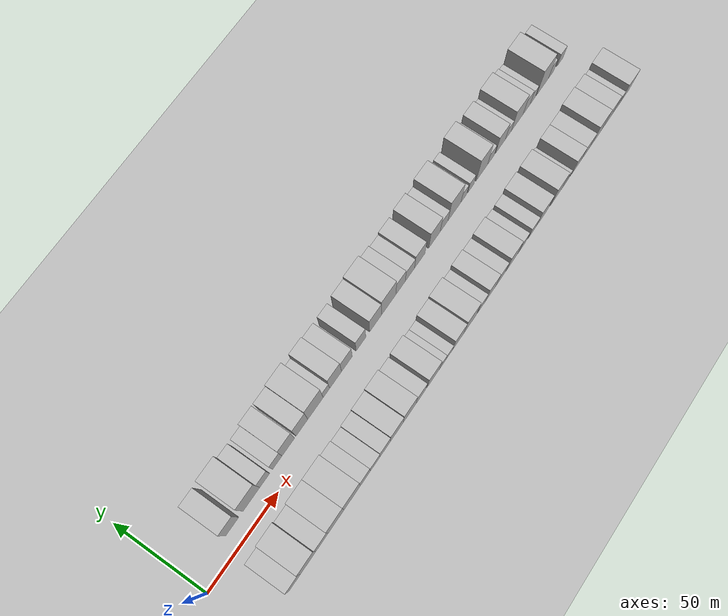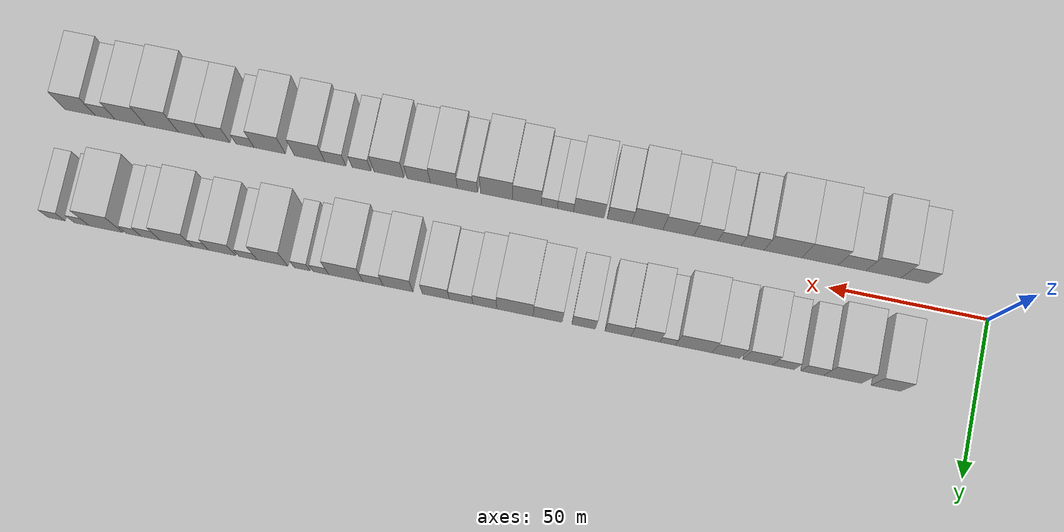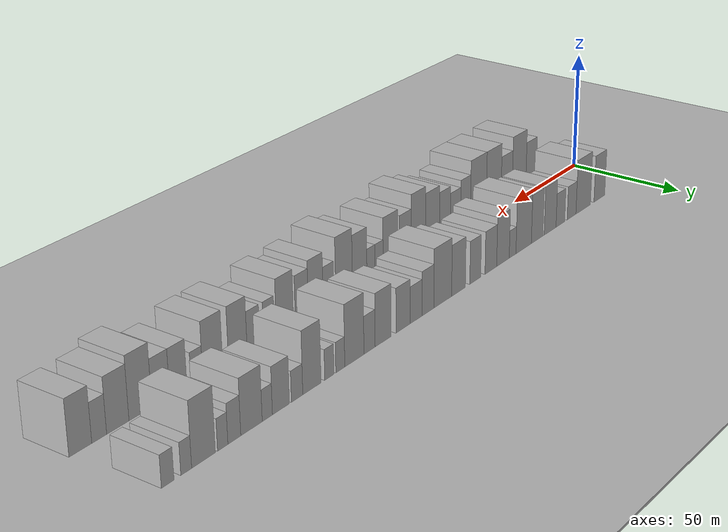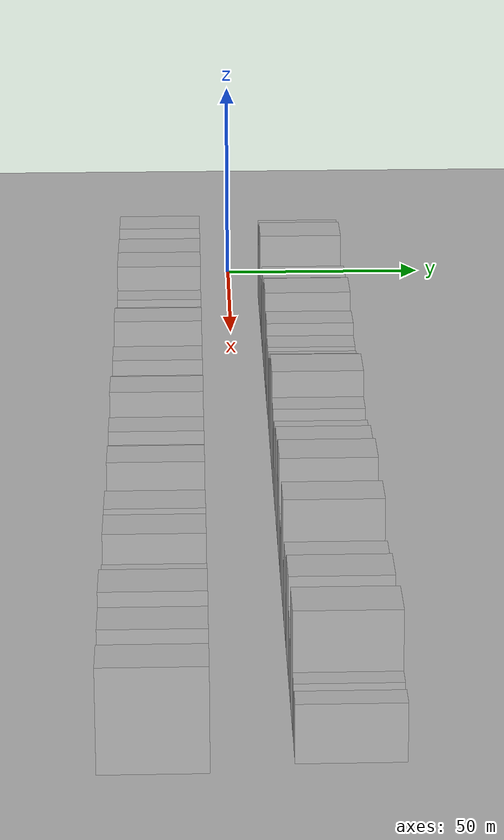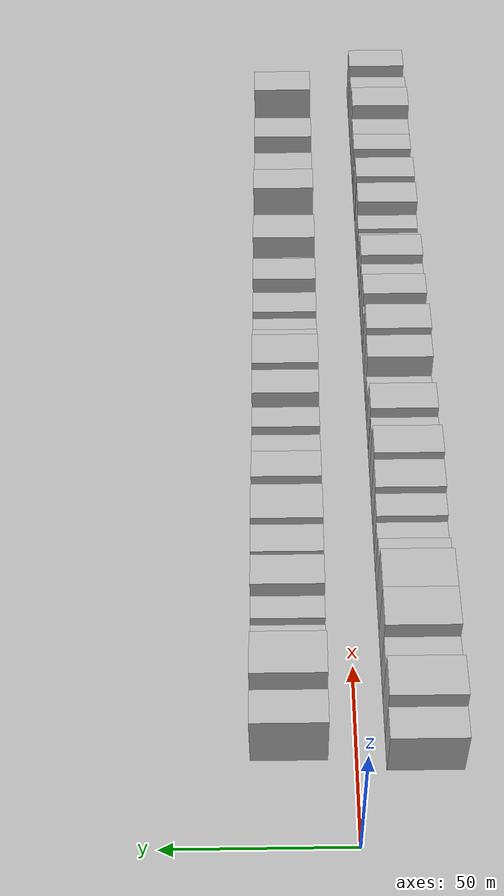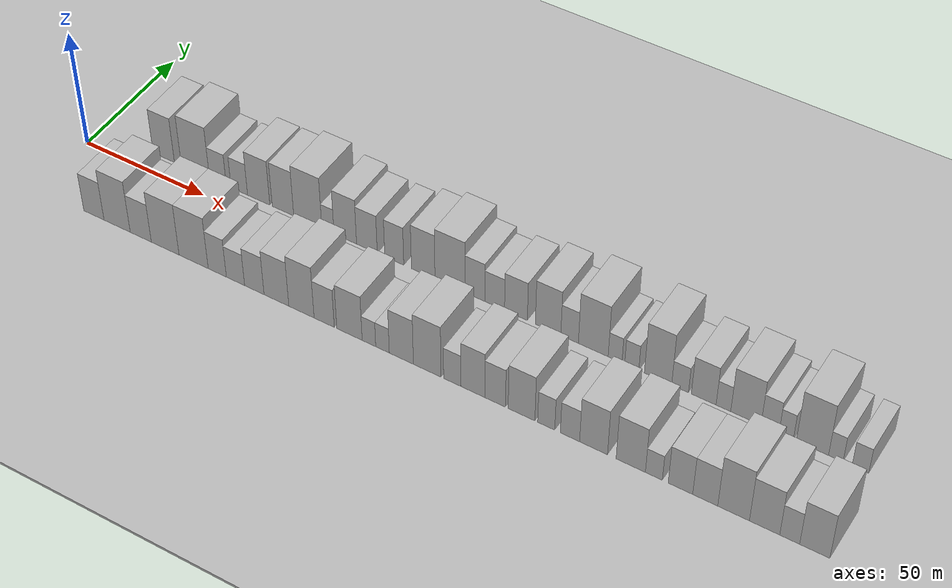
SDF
<?xml version="1.0" encoding="utf-8"?>

<sdf version="1.6">

   <world name="default">

      <gui fullscreen="0">

         <camera name="user_camera">

            <pose>-15 0 4.57585 0 0 0</pose>

            <view_controller>orbit</view_controller>

         </camera>

      </gui>

      <scene>

         <sky>

           <clouds>

             <speed>12</speed>

           </clouds>

         </sky>

         <ambient>0.4 0.4 0.4 1</ambient>

         <background>0.7 0.7 0.7 1</background>

         <shadows>1</shadows>

      </scene>

      <gravity>0 0 -9.8066</gravity>

      <magnetic_field>6e-06 2.3e-05 -4.2e-05</magnetic_field>

      <physics default="0" name="default_physics" type="ode">

         <ode>

            <solver>

               <type>quick</type>

               <iters>10</iters>

               <sor>1.0</sor>

               <use_dynamic_moi_rescaling>0</use_dynamic_moi_rescaling>

            </solver>

            <constraints>

               <cfm>0</cfm>

               <erp>0.2</erp>

               <contact_max_correcting_vel>100</contact_max_correcting_vel>

               <contact_surface_layer>0.001</contact_surface_layer>

            </constraints>

         </ode>

         <max_step_size>0.004</max_step_size>

         <real_time_factor>1</real_time_factor>

         <real_time_update_rate>250</real_time_update_rate>

      </physics>

      <light name="sun" type="directional">

         <cast_shadows>1</cast_shadows>

         <pose>0 0 10 0 0 0</pose>

         <diffuse>0.8 0.8 0.8 1</diffuse>

         <specular>0.2 0.2 0.2 1</specular>

         <attenuation>

            <range>1000</range>

            <constant>0.9</constant>

            <linear>0.01</linear>

            <quadratic>0.001</quadratic>

         </attenuation>

         <direction>-0.5 0.1 -0.9</direction>

      </light>

      <include>

         <name>ground_plane_1</name>

         <uri>model://HANNAS_ground_plane</uri>

         <pose>0 0 0  0 0 0</pose>

      </include>

      <include>

         <name>ground_plane_2</name>

         <uri>model://HANNAS_ground_plane</uri>

         <pose>100 0 0  0 0 0</pose>

      </include>

      <model name="building_1">

         <static>1</static>

         <pose frame="">27.5852 17.5000 0 0.000000 0.000000 1.570796</pose>

         <link name="link">

            <pose frame="">0 0 10.50 0 0 0</pose>

            <collision name="collision">

               <geometry>

                  <box>

                     <size>20.0000 9.1705 21.0000</size>

                  </box>

               </geometry>

               <max_contacts>10</max_contacts>

               <surface>

                  <contact>

                     <ode/>

                  </contact>

                  <bounce/>

                  <friction>

                     <torsional>

                        <ode/>

                     </torsional>

                     <ode/>

                  </friction>

               </surface>

            </collision>

            <visual name="visual">

               <cast_shadows>0</cast_shadows>

               <geometry>

                  <box>

                     <size>20.0000 9.1705 21.0000</size>

                  </box>

               </geometry>

               <material>

                  <script>

                     <uri>model://HANNAS_wall/materials/scripts</uri>

                     <uri>model://HANNAS_wall/materials/textures</uri>

                     <name>vrc/HANNAS_wall</name>

                  </script>

               </material>

            </visual>

            <self_collide>0</self_collide>

            <enable_wind>0</enable_wind>

            <kinematic>0</kinematic>

         </link>

      </model>

      <model name="building_2">

         <static>1</static>

         <pose frame="">41.1646 17.5000 0 0.000000 0.000000 1.570796</pose>

         <link name="link">

            <pose frame="">0 0 12.00 0 0 0</pose>

            <collision name="collision">

               <geometry>

                  <box>

                     <size>20.0000 11.9883 24.0000</size>

                  </box>

               </geometry>

               <max_contacts>10</max_contacts>

               <surface>

                  <contact>

                     <ode/>

                  </contact>

                  <bounce/>

                  <friction>

                     <torsional>

                        <ode/>

                     </torsional>

                     <ode/>

                  </friction>

               </surface>

            </collision>

            <visual name="visual">

               <cast_shadows>0</cast_shadows>

               <geometry>

                  <box>

                     <size>20.0000 11.9883 24.0000</size>

                  </box>

               </geometry>

               <material>

                  <script>

                     <uri>model://HANNAS_wall/materials/scripts</uri>

                     <uri>model://HANNAS_wall/materials/textures</uri>

                     <name>vrc/HANNAS_wall</name>

                  </script>

               </material>

            </visual>

            <self_collide>0</self_collide>

            <enable_wind>0</enable_wind>

            <kinematic>0</kinematic>

         </link>

      </model>

      <model name="building_3">

         <static>1</static>

         <pose frame="">50.7169 17.5000 0 0.000000 0.000000 1.570796</pose>

         <link name="link">

            <pose frame="">0 0 7.50 0 0 0</pose>

            <collision name="collision">

               <geometry>

                  <box>

                     <size>20.0000 7.1163 15.0000</size>

                  </box>

               </geometry>

               <max_contacts>10</max_contacts>

               <surface>

                  <contact>

                     <ode/>

                  </contact>

                  <bounce/>

                  <friction>

                     <torsional>

                        <ode/>

                     </torsional>

                     <ode/>

                  </friction>

               </surface>

            </collision>

            <visual name="visual">

               <cast_shadows>0</cast_shadows>

               <geometry>

                  <box>

                     <size>20.0000 7.1163 15.0000</size>

                  </box>

               </geometry>

               <material>

                  <script>

                     <uri>model://HANNAS_wall/materials/scripts</uri>

                     <uri>model://HANNAS_wall/materials/textures</uri>

                     <name>vrc/HANNAS_wall</name>

                  </script>

               </material>

            </visual>

            <self_collide>0</self_collide>

            <enable_wind>0</enable_wind>

            <kinematic>0</kinematic>

         </link>

      </model>

      <model name="building_4">

         <static>1</static>

         <pose frame="">59.7222 17.5000 0 0.000000 0.000000 1.570796</pose>

         <link name="link">

            <pose frame="">0 0 7.50 0 0 0</pose>

            <collision name="collision">

               <geometry>

                  <box>

                     <size>20.0000 6.8942 15.0000</size>

                  </box>

               </geometry>

               <max_contacts>10</max_contacts>

               <surface>

                  <contact>

                     <ode/>

                  </contact>

                  <bounce/>

                  <friction>

                     <torsional>

                        <ode/>

                     </torsional>

                     <ode/>

                  </friction>

               </surface>

            </collision>

            <visual name="visual">

               <cast_shadows>0</cast_shadows>

               <geometry>

                  <box>

                     <size>20.0000 6.8942 15.0000</size>

                  </box>

               </geometry>

               <material>

                  <script>

                     <uri>model://HANNAS_wall/materials/scripts</uri>

                     <uri>model://HANNAS_wall/materials/textures</uri>

                     <name>vrc/HANNAS_wall</name>

                  </script>

               </material>

            </visual>

            <self_collide>0</self_collide>

            <enable_wind>0</enable_wind>

            <kinematic>0</kinematic>

         </link>

      </model>

      <model name="building_5">

         <static>1</static>

         <pose frame="">67.7992 17.5000 0 0.000000 0.000000 1.570796</pose>

         <link name="link">

            <pose frame="">0 0 10.50 0 0 0</pose>

            <collision name="collision">

               <geometry>

                  <box>

                     <size>20.0000 9.2598 21.0000</size>

                  </box>

               </geometry>

               <max_contacts>10</max_contacts>

               <surface>

                  <contact>

                     <ode/>

                  </contact>

                  <bounce/>

                  <friction>

                     <torsional>

                        <ode/>

                     </torsional>

                     <ode/>

                  </friction>

               </surface>

            </collision>

            <visual name="visual">

               <cast_shadows>0</cast_shadows>

               <geometry>

                  <box>

                     <size>20.0000 9.2598 21.0000</size>

                  </box>

               </geometry>

               <material>

                  <script>

                     <uri>model://HANNAS_wall/materials/scripts</uri>

                     <uri>model://HANNAS_wall/materials/textures</uri>

                     <name>vrc/HANNAS_wall</name>

                  </script>

               </material>

            </visual>

            <self_collide>0</self_collide>

            <enable_wind>0</enable_wind>

            <kinematic>0</kinematic>

         </link>

      </model>

      <model name="building_6">

         <static>1</static>

         <pose frame="">77.8430 17.5000 0 0.000000 0.000000 1.570796</pose>

         <link name="link">

            <pose frame="">0 0 10.50 0 0 0</pose>

            <collision name="collision">

               <geometry>

                  <box>

                     <size>20.0000 8.8278 21.0000</size>

                  </box>

               </geometry>

               <max_contacts>10</max_contacts>

               <surface>

                  <contact>

                     <ode/>

                  </contact>

                  <bounce/>

                  <friction>

                     <torsional>

                        <ode/>

                     </torsional>

                     <ode/>

                  </friction>

               </surface>

            </collision>

            <visual name="visual">

               <cast_shadows>0</cast_shadows>

               <geometry>

                  <box>

                     <size>20.0000 8.8278 21.0000</size>

                  </box>

               </geometry>

               <material>

                  <script>

                     <uri>model://HANNAS_wall/materials/scripts</uri>

                     <uri>model://HANNAS_wall/materials/textures</uri>

                     <name>vrc/HANNAS_wall</name>

                  </script>

               </material>

            </visual>

            <self_collide>0</self_collide>

            <enable_wind>0</enable_wind>

            <kinematic>0</kinematic>

         </link>

      </model>

      <model name="building_7">

         <static>1</static>

         <pose frame="">87.9977 17.5000 0 0.000000 0.000000 1.570796</pose>

         <link name="link">

            <pose frame="">0 0 12.00 0 0 0</pose>

            <collision name="collision">

               <geometry>

                  <box>

                     <size>20.0000 11.4816 24.0000</size>

                  </box>

               </geometry>

               <max_contacts>10</max_contacts>

               <surface>

                  <contact>

                     <ode/>

                  </contact>

                  <bounce/>

                  <friction>

                     <torsional>

                        <ode/>

                     </torsional>

                     <ode/>

                  </friction>

               </surface>

            </collision>

            <visual name="visual">

               <cast_shadows>0</cast_shadows>

               <geometry>

                  <box>

                     <size>20.0000 11.4816 24.0000</size>

                  </box>

               </geometry>

               <material>

                  <script>

                     <uri>model://HANNAS_wall/materials/scripts</uri>

                     <uri>model://HANNAS_wall/materials/textures</uri>

                     <name>vrc/HANNAS_wall</name>

                  </script>

               </material>

            </visual>

            <self_collide>0</self_collide>

            <enable_wind>0</enable_wind>

            <kinematic>0</kinematic>

         </link>

      </model>

      <model name="building_8">

         <static>1</static>

         <pose frame="">96.1856 17.5000 0 0.000000 0.000000 1.570796</pose>

         <link name="link">

            <pose frame="">0 0 6.00 0 0 0</pose>

            <collision name="collision">

               <geometry>

                  <box>

                     <size>20.0000 4.8943 12.0000</size>

                  </box>

               </geometry>

               <max_contacts>10</max_contacts>

               <surface>

                  <contact>

                     <ode/>

                  </contact>

                  <bounce/>

                  <friction>

                     <torsional>

                        <ode/>

                     </torsional>

                     <ode/>

                  </friction>

               </surface>

            </collision>

            <visual name="visual">

               <cast_shadows>0</cast_shadows>

               <geometry>

                  <box>

                     <size>20.0000 4.8943 12.0000</size>

                  </box>

               </geometry>

               <material>

                  <script>

                     <uri>model://HANNAS_wall/materials/scripts</uri>

                     <uri>model://HANNAS_wall/materials/textures</uri>

                     <name>vrc/HANNAS_wall</name>

                  </script>

               </material>

            </visual>

            <self_collide>0</self_collide>

            <enable_wind>0</enable_wind>

            <kinematic>0</kinematic>

         </link>

      </model>

      <model name="building_9">

         <static>1</static>

         <pose frame="">103.1687 17.5000 0 0.000000 0.000000 1.570796</pose>

         <link name="link">

            <pose frame="">0 0 10.50 0 0 0</pose>

            <collision name="collision">

               <geometry>

                  <box>

                     <size>20.0000 9.0717 21.0000</size>

                  </box>

               </geometry>

               <max_contacts>10</max_contacts>

               <surface>

                  <contact>

                     <ode/>

                  </contact>

                  <bounce/>

                  <friction>

                     <torsional>

                        <ode/>

                     </torsional>

                     <ode/>

                  </friction>

               </surface>

            </collision>

            <visual name="visual">

               <cast_shadows>0</cast_shadows>

               <geometry>

                  <box>

                     <size>20.0000 9.0717 21.0000</size>

                  </box>

               </geometry>

               <material>

                  <script>

                     <uri>model://HANNAS_wall/materials/scripts</uri>

                     <uri>model://HANNAS_wall/materials/textures</uri>

                     <name>vrc/HANNAS_wall</name>

                  </script>

               </material>

            </visual>

            <self_collide>0</self_collide>

            <enable_wind>0</enable_wind>

            <kinematic>0</kinematic>

         </link>

      </model>

      <model name="building_10">

         <static>1</static>

         <pose frame="">111.8234 17.5000 0 0.000000 0.000000 1.570796</pose>

         <link name="link">

            <pose frame="">0 0 9.00 0 0 0</pose>

            <collision name="collision">

               <geometry>

                  <box>

                     <size>20.0000 8.2377 18.0000</size>

                  </box>

               </geometry>

               <max_contacts>10</max_contacts>

               <surface>

                  <contact>

                     <ode/>

                  </contact>

                  <bounce/>

                  <friction>

                     <torsional>

                        <ode/>

                     </torsional>

                     <ode/>

                  </friction>

               </surface>

            </collision>

            <visual name="visual">

               <cast_shadows>0</cast_shadows>

               <geometry>

                  <box>

                     <size>20.0000 8.2377 18.0000</size>

                  </box>

               </geometry>

               <material>

                  <script>

                     <uri>model://HANNAS_wall/materials/scripts</uri>

                     <uri>model://HANNAS_wall/materials/textures</uri>

                     <name>vrc/HANNAS_wall</name>

                  </script>

               </material>

            </visual>

            <self_collide>0</self_collide>

            <enable_wind>0</enable_wind>

            <kinematic>0</kinematic>

         </link>

      </model>

      <model name="building_11">

         <static>1</static>

         <pose frame="">122.6822 17.5000 0 0.000000 0.000000 1.570796</pose>

         <link name="link">

            <pose frame="">0 0 9.00 0 0 0</pose>

            <collision name="collision">

               <geometry>

                  <box>

                     <size>20.0000 7.4799 18.0000</size>

                  </box>

               </geometry>

               <max_contacts>10</max_contacts>

               <surface>

                  <contact>

                     <ode/>

                  </contact>

                  <bounce/>

                  <friction>

                     <torsional>

                        <ode/>

                     </torsional>

                     <ode/>

                  </friction>

               </surface>

            </collision>

            <visual name="visual">

               <cast_shadows>0</cast_shadows>

               <geometry>

                  <box>

                     <size>20.0000 7.4799 18.0000</size>

                  </box>

               </geometry>

               <material>

                  <script>

                     <uri>model://HANNAS_wall/materials/scripts</uri>

                     <uri>model://HANNAS_wall/materials/textures</uri>

                     <name>vrc/HANNAS_wall</name>

                  </script>

               </material>

            </visual>

            <self_collide>0</self_collide>

            <enable_wind>0</enable_wind>

            <kinematic>0</kinematic>

         </link>

      </model>

      <model name="building_12">

         <static>1</static>

         <pose frame="">134.0136 17.5000 0 0.000000 0.000000 1.570796</pose>

         <link name="link">

            <pose frame="">0 0 10.50 0 0 0</pose>

            <collision name="collision">

               <geometry>

                  <box>

                     <size>20.0000 9.1830 21.0000</size>

                  </box>

               </geometry>

               <max_contacts>10</max_contacts>

               <surface>

                  <contact>

                     <ode/>

                  </contact>

                  <bounce/>

                  <friction>

                     <torsional>

                        <ode/>

                     </torsional>

                     <ode/>

                  </friction>

               </surface>

            </collision>

            <visual name="visual">

               <cast_shadows>0</cast_shadows>

               <geometry>

                  <box>

                     <size>20.0000 9.1830 21.0000</size>

                  </box>

               </geometry>

               <material>

                  <script>

                     <uri>model://HANNAS_wall/materials/scripts</uri>

                     <uri>model://HANNAS_wall/materials/textures</uri>

                     <name>vrc/HANNAS_wall</name>

                  </script>

               </material>

            </visual>

            <self_collide>0</self_collide>

            <enable_wind>0</enable_wind>

            <kinematic>0</kinematic>

         </link>

      </model>

      <model name="building_13">

         <static>1</static>

         <pose frame="">144.3929 17.5000 0 0.000000 0.000000 1.570796</pose>

         <link name="link">

            <pose frame="">0 0 12.00 0 0 0</pose>

            <collision name="collision">

               <geometry>

                  <box>

                     <size>20.0000 11.5757 24.0000</size>

                  </box>

               </geometry>

               <max_contacts>10</max_contacts>

               <surface>

                  <contact>

                     <ode/>

                  </contact>

                  <bounce/>

                  <friction>

                     <torsional>

                        <ode/>

                     </torsional>

                     <ode/>

                  </friction>

               </surface>

            </collision>

            <visual name="visual">

               <cast_shadows>0</cast_shadows>

               <geometry>

                  <box>

                     <size>20.0000 11.5757 24.0000</size>

                  </box>

               </geometry>

               <material>

                  <script>

                     <uri>model://HANNAS_wall/materials/scripts</uri>

                     <uri>model://HANNAS_wall/materials/textures</uri>

                     <name>vrc/HANNAS_wall</name>

                  </script>

               </material>

            </visual>

            <self_collide>0</self_collide>

            <enable_wind>0</enable_wind>

            <kinematic>0</kinematic>

         </link>

      </model>

      <model name="building_14">

         <static>1</static>

         <pose frame="">153.9716 17.5000 0 0.000000 0.000000 1.570796</pose>

         <link name="link">

            <pose frame="">0 0 9.00 0 0 0</pose>

            <collision name="collision">

               <geometry>

                  <box>

                     <size>20.0000 7.5817 18.0000</size>

                  </box>

               </geometry>

               <max_contacts>10</max_contacts>

               <surface>

                  <contact>

                     <ode/>

                  </contact>

                  <bounce/>

                  <friction>

                     <torsional>

                        <ode/>

                     </torsional>

                     <ode/>

                  </friction>

               </surface>

            </collision>

            <visual name="visual">

               <cast_shadows>0</cast_shadows>

               <geometry>

                  <box>

                     <size>20.0000 7.5817 18.0000</size>

                  </box>

               </geometry>

               <material>

                  <script>

                     <uri>model://HANNAS_wall/materials/scripts</uri>

                     <uri>model://HANNAS_wall/materials/textures</uri>

                     <name>vrc/HANNAS_wall</name>

                  </script>

               </material>

            </visual>

            <self_collide>0</self_collide>

            <enable_wind>0</enable_wind>

            <kinematic>0</kinematic>

         </link>

      </model>

      <model name="building_15">

         <static>1</static>

         <pose frame="">161.5057 17.5000 0 0.000000 0.000000 1.570796</pose>

         <link name="link">

            <pose frame="">0 0 7.50 0 0 0</pose>

            <collision name="collision">

               <geometry>

                  <box>

                     <size>20.0000 7.4865 15.0000</size>

                  </box>

               </geometry>

               <max_contacts>10</max_contacts>

               <surface>

                  <contact>

                     <ode/>

                  </contact>

                  <bounce/>

                  <friction>

                     <torsional>

                        <ode/>

                     </torsional>

                     <ode/>

                  </friction>

               </surface>

            </collision>

            <visual name="visual">

               <cast_shadows>0</cast_shadows>

               <geometry>

                  <box>

                     <size>20.0000 7.4865 15.0000</size>

                  </box>

               </geometry>

               <material>

                  <script>

                     <uri>model://HANNAS_wall/materials/scripts</uri>

                     <uri>model://HANNAS_wall/materials/textures</uri>

                     <name>vrc/HANNAS_wall</name>

                  </script>

               </material>

            </visual>

            <self_collide>0</self_collide>

            <enable_wind>0</enable_wind>

            <kinematic>0</kinematic>

         </link>

      </model>

      <model name="building_16">

         <static>1</static>

         <pose frame="">169.5354 17.5000 0 0.000000 0.000000 1.570796</pose>

         <link name="link">

            <pose frame="">0 0 9.00 0 0 0</pose>

            <collision name="collision">

               <geometry>

                  <box>

                     <size>20.0000 8.5730 18.0000</size>

                  </box>

               </geometry>

               <max_contacts>10</max_contacts>

               <surface>

                  <contact>

                     <ode/>

                  </contact>

                  <bounce/>

                  <friction>

                     <torsional>

                        <ode/>

                     </torsional>

                     <ode/>

                  </friction>

               </surface>

            </collision>

            <visual name="visual">

               <cast_shadows>0</cast_shadows>

               <geometry>

                  <box>

                     <size>20.0000 8.5730 18.0000</size>

                  </box>

               </geometry>

               <material>

                  <script>

                     <uri>model://HANNAS_wall/materials/scripts</uri>

                     <uri>model://HANNAS_wall/materials/textures</uri>

                     <name>vrc/HANNAS_wall</name>

                  </script>

               </material>

            </visual>

            <self_collide>0</self_collide>

            <enable_wind>0</enable_wind>

            <kinematic>0</kinematic>

         </link>

      </model>

      <model name="building_17">

         <static>1</static>

         <pose frame="">181.5526 17.5000 0 0.000000 0.000000 1.570796</pose>

         <link name="link">

            <pose frame="">0 0 10.50 0 0 0</pose>

            <collision name="collision">

               <geometry>

                  <box>

                     <size>20.0000 9.4613 21.0000</size>

                  </box>

               </geometry>

               <max_contacts>10</max_contacts>

               <surface>

                  <contact>

                     <ode/>

                  </contact>

                  <bounce/>

                  <friction>

                     <torsional>

                        <ode/>

                     </torsional>

                     <ode/>

                  </friction>

               </surface>

            </collision>

            <visual name="visual">

               <cast_shadows>0</cast_shadows>

               <geometry>

                  <box>

                     <size>20.0000 9.4613 21.0000</size>

                  </box>

               </geometry>

               <material>

                  <script>

                     <uri>model://HANNAS_wall/materials/scripts</uri>

                     <uri>model://HANNAS_wall/materials/textures</uri>

                     <name>vrc/HANNAS_wall</name>

                  </script>

               </material>

            </visual>

            <self_collide>0</self_collide>

            <enable_wind>0</enable_wind>

            <kinematic>0</kinematic>

         </link>

      </model>

      <model name="building_18">

         <static>1</static>

         <pose frame="">189.5283 17.5000 0 0.000000 0.000000 1.570796</pose>

         <link name="link">

            <pose frame="">0 0 7.50 0 0 0</pose>

            <collision name="collision">

               <geometry>

                  <box>

                     <size>20.0000 6.4901 15.0000</size>

                  </box>

               </geometry>

               <max_contacts>10</max_contacts>

               <surface>

                  <contact>

                     <ode/>

                  </contact>

                  <bounce/>

                  <friction>

                     <torsional>

                        <ode/>

                     </torsional>

                     <ode/>

                  </friction>

               </surface>

            </collision>

            <visual name="visual">

               <cast_shadows>0</cast_shadows>

               <geometry>

                  <box>

                     <size>20.0000 6.4901 15.0000</size>

                  </box>

               </geometry>

               <material>

                  <script>

                     <uri>model://HANNAS_wall/materials/scripts</uri>

                     <uri>model://HANNAS_wall/materials/textures</uri>

                     <name>vrc/HANNAS_wall</name>

                  </script>

               </material>

            </visual>

            <self_collide>0</self_collide>

            <enable_wind>0</enable_wind>

            <kinematic>0</kinematic>

         </link>

      </model>

      <model name="building_19">

         <static>1</static>

         <pose frame="">198.2223 17.5000 0 0.000000 0.000000 1.570796</pose>

         <link name="link">

            <pose frame="">0 0 12.00 0 0 0</pose>

            <collision name="collision">

               <geometry>

                  <box>

                     <size>20.0000 10.8981 24.0000</size>

                  </box>

               </geometry>

               <max_contacts>10</max_contacts>

               <surface>

                  <contact>

                     <ode/>

                  </contact>

                  <bounce/>

                  <friction>

                     <torsional>

                        <ode/>

                     </torsional>

                     <ode/>

                  </friction>

               </surface>

            </collision>

            <visual name="visual">

               <cast_shadows>0</cast_shadows>

               <geometry>

                  <box>

                     <size>20.0000 10.8981 24.0000</size>

                  </box>

               </geometry>

               <material>

                  <script>

                     <uri>model://HANNAS_wall/materials/scripts</uri>

                     <uri>model://HANNAS_wall/materials/textures</uri>

                     <name>vrc/HANNAS_wall</name>

                  </script>

               </material>

            </visual>

            <self_collide>0</self_collide>

            <enable_wind>0</enable_wind>

            <kinematic>0</kinematic>

         </link>

      </model>

      <model name="building_20">

         <static>1</static>

         <pose frame="">206.1692 17.5000 0 0.000000 0.000000 1.570796</pose>

         <link name="link">

            <pose frame="">0 0 6.00 0 0 0</pose>

            <collision name="collision">

               <geometry>

                  <box>

                     <size>20.0000 4.9956 12.0000</size>

                  </box>

               </geometry>

               <max_contacts>10</max_contacts>

               <surface>

                  <contact>

                     <ode/>

                  </contact>

                  <bounce/>

                  <friction>

                     <torsional>

                        <ode/>

                     </torsional>

                     <ode/>

                  </friction>

               </surface>

            </collision>

            <visual name="visual">

               <cast_shadows>0</cast_shadows>

               <geometry>

                  <box>

                     <size>20.0000 4.9956 12.0000</size>

                  </box>

               </geometry>

               <material>

                  <script>

                     <uri>model://HANNAS_wall/materials/scripts</uri>

                     <uri>model://HANNAS_wall/materials/textures</uri>

                     <name>vrc/HANNAS_wall</name>

                  </script>

               </material>

            </visual>

            <self_collide>0</self_collide>

            <enable_wind>0</enable_wind>

            <kinematic>0</kinematic>

         </link>

      </model>

      <model name="building_21">

         <static>1</static>

         <pose frame="">212.2109 17.5000 0 0.000000 0.000000 1.570796</pose>

         <link name="link">

            <pose frame="">0 0 6.00 0 0 0</pose>

            <collision name="collision">

               <geometry>

                  <box>

                     <size>20.0000 5.0878 12.0000</size>

                  </box>

               </geometry>

               <max_contacts>10</max_contacts>

               <surface>

                  <contact>

                     <ode/>

                  </contact>

                  <bounce/>

                  <friction>

                     <torsional>

                        <ode/>

                     </torsional>

                     <ode/>

                  </friction>

               </surface>

            </collision>

            <visual name="visual">

               <cast_shadows>0</cast_shadows>

               <geometry>

                  <box>

                     <size>20.0000 5.0878 12.0000</size>

                  </box>

               </geometry>

               <material>

                  <script>

                     <uri>model://HANNAS_wall/materials/scripts</uri>

                     <uri>model://HANNAS_wall/materials/textures</uri>

                     <name>vrc/HANNAS_wall</name>

                  </script>

               </material>

            </visual>

            <self_collide>0</self_collide>

            <enable_wind>0</enable_wind>

            <kinematic>0</kinematic>

         </link>

      </model>

      <model name="building_22">

         <static>1</static>

         <pose frame="">221.6226 17.5000 0 0.000000 0.000000 1.570796</pose>

         <link name="link">

            <pose frame="">0 0 12.00 0 0 0</pose>

            <collision name="collision">

               <geometry>

                  <box>

                     <size>20.0000 9.7358 24.0000</size>

                  </box>

               </geometry>

               <max_contacts>10</max_contacts>

               <surface>

                  <contact>

                     <ode/>

                  </contact>

                  <bounce/>

                  <friction>

                     <torsional>

                        <ode/>

                     </torsional>

                     <ode/>

                  </friction>

               </surface>

            </collision>

            <visual name="visual">

               <cast_shadows>0</cast_shadows>

               <geometry>

                  <box>

                     <size>20.0000 9.7358 24.0000</size>

                  </box>

               </geometry>

               <material>

                  <script>

                     <uri>model://HANNAS_wall/materials/scripts</uri>

                     <uri>model://HANNAS_wall/materials/textures</uri>

                     <name>vrc/HANNAS_wall</name>

                  </script>

               </material>

            </visual>

            <self_collide>0</self_collide>

            <enable_wind>0</enable_wind>

            <kinematic>0</kinematic>

         </link>

      </model>

      <model name="building_23">

         <static>1</static>

         <pose frame="">229.4698 17.5000 0 0.000000 0.000000 1.570796</pose>

         <link name="link">

            <pose frame="">0 0 6.00 0 0 0</pose>

            <collision name="collision">

               <geometry>

                  <box>

                     <size>20.0000 5.9585 12.0000</size>

                  </box>

               </geometry>

               <max_contacts>10</max_contacts>

               <surface>

                  <contact>

                     <ode/>

                  </contact>

                  <bounce/>

                  <friction>

                     <torsional>

                        <ode/>

                     </torsional>

                     <ode/>

                  </friction>

               </surface>

            </collision>

            <visual name="visual">

               <cast_shadows>0</cast_shadows>

               <geometry>

                  <box>

                     <size>20.0000 5.9585 12.0000</size>

                  </box>

               </geometry>

               <material>

                  <script>

                     <uri>model://HANNAS_wall/materials/scripts</uri>

                     <uri>model://HANNAS_wall/materials/textures</uri>

                     <name>vrc/HANNAS_wall</name>

                  </script>

               </material>

            </visual>

            <self_collide>0</self_collide>

            <enable_wind>0</enable_wind>

            <kinematic>0</kinematic>

         </link>

      </model>

      <model name="building_24">

         <static>1</static>

         <pose frame="">237.7962 17.5000 0 0.000000 0.000000 1.570796</pose>

         <link name="link">

            <pose frame="">0 0 9.00 0 0 0</pose>

            <collision name="collision">

               <geometry>

                  <box>

                     <size>20.0000 8.6944 18.0000</size>

                  </box>

               </geometry>

               <max_contacts>10</max_contacts>

               <surface>

                  <contact>

                     <ode/>

                  </contact>

                  <bounce/>

                  <friction>

                     <torsional>

                        <ode/>

                     </torsional>

                     <ode/>

                  </friction>

               </surface>

            </collision>

            <visual name="visual">

               <cast_shadows>0</cast_shadows>

               <geometry>

                  <box>

                     <size>20.0000 8.6944 18.0000</size>

                  </box>

               </geometry>

               <material>

                  <script>

                     <uri>model://HANNAS_wall/materials/scripts</uri>

                     <uri>model://HANNAS_wall/materials/textures</uri>

                     <name>vrc/HANNAS_wall</name>

                  </script>

               </material>

            </visual>

            <self_collide>0</self_collide>

            <enable_wind>0</enable_wind>

            <kinematic>0</kinematic>

         </link>

      </model>

      <model name="building_25">

         <static>1</static>

         <pose frame="">244.6974 17.5000 0 0.000000 0.000000 1.570796</pose>

         <link name="link">

            <pose frame="">0 0 6.00 0 0 0</pose>

            <collision name="collision">

               <geometry>

                  <box>

                     <size>20.0000 5.1079 12.0000</size>

                  </box>

               </geometry>

               <max_contacts>10</max_contacts>

               <surface>

                  <contact>

                     <ode/>

                  </contact>

                  <bounce/>

                  <friction>

                     <torsional>

                        <ode/>

                     </torsional>

                     <ode/>

                  </friction>

               </surface>

            </collision>

            <visual name="visual">

               <cast_shadows>0</cast_shadows>

               <geometry>

                  <box>

                     <size>20.0000 5.1079 12.0000</size>

                  </box>

               </geometry>

               <material>

                  <script>

                     <uri>model://HANNAS_wall/materials/scripts</uri>

                     <uri>model://HANNAS_wall/materials/textures</uri>

                     <name>vrc/HANNAS_wall</name>

                  </script>

               </material>

            </visual>

            <self_collide>0</self_collide>

            <enable_wind>0</enable_wind>

            <kinematic>0</kinematic>

         </link>

      </model>

      <model name="building_26">

         <static>1</static>

         <pose frame="">252.4912 17.5000 0 0.000000 0.000000 1.570796</pose>

         <link name="link">

            <pose frame="">0 0 10.50 0 0 0</pose>

            <collision name="collision">

               <geometry>

                  <box>

                     <size>20.0000 10.4798 21.0000</size>

                  </box>

               </geometry>

               <max_contacts>10</max_contacts>

               <surface>

                  <contact>

                     <ode/>

                  </contact>

                  <bounce/>

                  <friction>

                     <torsional>

                        <ode/>

                     </torsional>

                     <ode/>

                  </friction>

               </surface>

            </collision>

            <visual name="visual">

               <cast_shadows>0</cast_shadows>

               <geometry>

                  <box>

                     <size>20.0000 10.4798 21.0000</size>

                  </box>

               </geometry>

               <material>

                  <script>

                     <uri>model://HANNAS_wall/materials/scripts</uri>

                     <uri>model://HANNAS_wall/materials/textures</uri>

                     <name>vrc/HANNAS_wall</name>

                  </script>

               </material>

            </visual>

            <self_collide>0</self_collide>

            <enable_wind>0</enable_wind>

            <kinematic>0</kinematic>

         </link>

      </model>

      <model name="building_27">

         <static>1</static>

         <pose frame="">260.8215 17.5000 0 0.000000 0.000000 1.570796</pose>

         <link name="link">

            <pose frame="">0 0 7.50 0 0 0</pose>

            <collision name="collision">

               <geometry>

                  <box>

                     <size>20.0000 6.1807 15.0000</size>

                  </box>

               </geometry>

               <max_contacts>10</max_contacts>

               <surface>

                  <contact>

                     <ode/>

                  </contact>

                  <bounce/>

                  <friction>

                     <torsional>

                        <ode/>

                     </torsional>

                     <ode/>

                  </friction>

               </surface>

            </collision>

            <visual name="visual">

               <cast_shadows>0</cast_shadows>

               <geometry>

                  <box>

                     <size>20.0000 6.1807 15.0000</size>

                  </box>

               </geometry>

               <material>

                  <script>

                     <uri>model://HANNAS_wall/materials/scripts</uri>

                     <uri>model://HANNAS_wall/materials/textures</uri>

                     <name>vrc/HANNAS_wall</name>

                  </script>

               </material>

            </visual>

            <self_collide>0</self_collide>

            <enable_wind>0</enable_wind>

            <kinematic>0</kinematic>

         </link>

      </model>

      <model name="building_28">

         <static>1</static>

         <pose frame="">266.3518 17.5000 0 0.000000 0.000000 1.570796</pose>

         <link name="link">

            <pose frame="">0 0 6.00 0 0 0</pose>

            <collision name="collision">

               <geometry>

                  <box>

                     <size>20.0000 4.8800 12.0000</size>

                  </box>

               </geometry>

               <max_contacts>10</max_contacts>

               <surface>

                  <contact>

                     <ode/>

                  </contact>

                  <bounce/>

                  <friction>

                     <torsional>

                        <ode/>

                     </torsional>

                     <ode/>

                  </friction>

               </surface>

            </collision>

            <visual name="visual">

               <cast_shadows>0</cast_shadows>

               <geometry>

                  <box>

                     <size>20.0000 4.8800 12.0000</size>

                  </box>

               </geometry>

               <material>

                  <script>

                     <uri>model://HANNAS_wall/materials/scripts</uri>

                     <uri>model://HANNAS_wall/materials/textures</uri>

                     <name>vrc/HANNAS_wall</name>

                  </script>

               </material>

            </visual>

            <self_collide>0</self_collide>

            <enable_wind>0</enable_wind>

            <kinematic>0</kinematic>

         </link>

      </model>

      <model name="building_29">

         <static>1</static>

         <pose frame="">275.2302 17.5000 0 0.000000 0.000000 1.570796</pose>

         <link name="link">

            <pose frame="">0 0 12.00 0 0 0</pose>

            <collision name="collision">

               <geometry>

                  <box>

                     <size>20.0000 10.8769 24.0000</size>

                  </box>

               </geometry>

               <max_contacts>10</max_contacts>

               <surface>

                  <contact>

                     <ode/>

                  </contact>

                  <bounce/>

                  <friction>

                     <torsional>

                        <ode/>

                     </torsional>

                     <ode/>

                  </friction>

               </surface>

            </collision>

            <visual name="visual">

               <cast_shadows>0</cast_shadows>

               <geometry>

                  <box>

                     <size>20.0000 10.8769 24.0000</size>

                  </box>

               </geometry>

               <material>

                  <script>

                     <uri>model://HANNAS_wall/materials/scripts</uri>

                     <uri>model://HANNAS_wall/materials/textures</uri>

                     <name>vrc/HANNAS_wall</name>

                  </script>

               </material>

            </visual>

            <self_collide>0</self_collide>

            <enable_wind>0</enable_wind>

            <kinematic>0</kinematic>

         </link>

      </model>

      <model name="building_30">

         <static>1</static>

         <pose frame="">283.0954 17.5000 0 0.000000 0.000000 1.570796</pose>

         <link name="link">

            <pose frame="">0 0 6.00 0 0 0</pose>

            <collision name="collision">

               <geometry>

                  <box>

                     <size>20.0000 4.8534 12.0000</size>

                  </box>

               </geometry>

               <max_contacts>10</max_contacts>

               <surface>

                  <contact>

                     <ode/>

                  </contact>

                  <bounce/>

                  <friction>

                     <torsional>

                        <ode/>

                     </torsional>

                     <ode/>

                  </friction>

               </surface>

            </collision>

            <visual name="visual">

               <cast_shadows>0</cast_shadows>

               <geometry>

                  <box>

                     <size>20.0000 4.8534 12.0000</size>

                  </box>

               </geometry>

               <material>

                  <script>

                     <uri>model://HANNAS_wall/materials/scripts</uri>

                     <uri>model://HANNAS_wall/materials/textures</uri>

                     <name>vrc/HANNAS_wall</name>

                  </script>

               </material>

            </visual>

            <self_collide>0</self_collide>

            <enable_wind>0</enable_wind>

            <kinematic>0</kinematic>

         </link>

      </model>

      <model name="building_31">

         <static>1</static>

         <pose frame="">291.2903 17.5000 0 0.000000 0.000000 1.570796</pose>

         <link name="link">

            <pose frame="">0 0 6.00 0 0 0</pose>

            <collision name="collision">

               <geometry>

                  <box>

                     <size>20.0000 5.5366 12.0000</size>

                  </box>

               </geometry>

               <max_contacts>10</max_contacts>

               <surface>

                  <contact>

                     <ode/>

                  </contact>

                  <bounce/>

                  <friction>

                     <torsional>

                        <ode/>

                     </torsional>

                     <ode/>

                  </friction>

               </surface>

            </collision>

            <visual name="visual">

               <cast_shadows>0</cast_shadows>

               <geometry>

                  <box>

                     <size>20.0000 5.5366 12.0000</size>

                  </box>

               </geometry>

               <material>

                  <script>

                     <uri>model://HANNAS_wall/materials/scripts</uri>

                     <uri>model://HANNAS_wall/materials/textures</uri>

                     <name>vrc/HANNAS_wall</name>

                  </script>

               </material>

            </visual>

            <self_collide>0</self_collide>

            <enable_wind>0</enable_wind>

            <kinematic>0</kinematic>

         </link>

      </model>

      <model name="building_32">

         <static>1</static>

         <pose frame="">24.3116 -17.5000 0 0.000000 0.000000 1.570796</pose>

         <link name="link">

            <pose frame="">0 0 9.00 0 0 0</pose>

            <collision name="collision">

               <geometry>

                  <box>

                     <size>20.0000 8.6232 18.0000</size>

                  </box>

               </geometry>

               <max_contacts>10</max_contacts>

               <surface>

                  <contact>

                     <ode/>

                  </contact>

                  <bounce/>

                  <friction>

                     <torsional>

                        <ode/>

                     </torsional>

                     <ode/>

                  </friction>

               </surface>

            </collision>

            <visual name="visual">

               <cast_shadows>0</cast_shadows>

               <geometry>

                  <box>

                     <size>20.0000 8.6232 18.0000</size>

                  </box>

               </geometry>

               <material>

                  <script>

                     <uri>model://HANNAS_wall/materials/scripts</uri>

                     <uri>model://HANNAS_wall/materials/textures</uri>

                     <name>vrc/HANNAS_wall</name>

                  </script>

               </material>

            </visual>

            <self_collide>0</self_collide>

            <enable_wind>0</enable_wind>

            <kinematic>0</kinematic>

         </link>

      </model>

      <model name="building_33">

         <static>1</static>

         <pose frame="">34.1725 -17.5000 0 0.000000 0.000000 1.570796</pose>

         <link name="link">

            <pose frame="">0 0 12.00 0 0 0</pose>

            <collision name="collision">

               <geometry>

                  <box>

                     <size>20.0000 11.0985 24.0000</size>

                  </box>

               </geometry>

               <max_contacts>10</max_contacts>

               <surface>

                  <contact>

                     <ode/>

                  </contact>

                  <bounce/>

                  <friction>

                     <torsional>

                        <ode/>

                     </torsional>

                     <ode/>

                  </friction>

               </surface>

            </collision>

            <visual name="visual">

               <cast_shadows>0</cast_shadows>

               <geometry>

                  <box>

                     <size>20.0000 11.0985 24.0000</size>

                  </box>

               </geometry>

               <material>

                  <script>

                     <uri>model://HANNAS_wall/materials/scripts</uri>

                     <uri>model://HANNAS_wall/materials/textures</uri>

                     <name>vrc/HANNAS_wall</name>

                  </script>

               </material>

            </visual>

            <self_collide>0</self_collide>

            <enable_wind>0</enable_wind>

            <kinematic>0</kinematic>

         </link>

      </model>

      <model name="building_34">

         <static>1</static>

         <pose frame="">44.1316 -17.5000 0 0.000000 0.000000 1.570796</pose>

         <link name="link">

            <pose frame="">0 0 9.00 0 0 0</pose>

            <collision name="collision">

               <geometry>

                  <box>

                     <size>20.0000 8.8197 18.0000</size>

                  </box>

               </geometry>

               <max_contacts>10</max_contacts>

               <surface>

                  <contact>

                     <ode/>

                  </contact>

                  <bounce/>

                  <friction>

                     <torsional>

                        <ode/>

                     </torsional>

                     <ode/>

                  </friction>

               </surface>

            </collision>

            <visual name="visual">

               <cast_shadows>0</cast_shadows>

               <geometry>

                  <box>

                     <size>20.0000 8.8197 18.0000</size>

                  </box>

               </geometry>

               <material>

                  <script>

                     <uri>model://HANNAS_wall/materials/scripts</uri>

                     <uri>model://HANNAS_wall/materials/textures</uri>

                     <name>vrc/HANNAS_wall</name>

                  </script>

               </material>

            </visual>

            <self_collide>0</self_collide>

            <enable_wind>0</enable_wind>

            <kinematic>0</kinematic>

         </link>

      </model>

      <model name="building_35">

         <static>1</static>

         <pose frame="">54.2930 -17.5000 0 0.000000 0.000000 1.570796</pose>

         <link name="link">

            <pose frame="">0 0 12.00 0 0 0</pose>

            <collision name="collision">

               <geometry>

                  <box>

                     <size>20.0000 11.5032 24.0000</size>

                  </box>

               </geometry>

               <max_contacts>10</max_contacts>

               <surface>

                  <contact>

                     <ode/>

                  </contact>

                  <bounce/>

                  <friction>

                     <torsional>

                        <ode/>

                     </torsional>

                     <ode/>

                  </friction>

               </surface>

            </collision>

            <visual name="visual">

               <cast_shadows>0</cast_shadows>

               <geometry>

                  <box>

                     <size>20.0000 11.5032 24.0000</size>

                  </box>

               </geometry>

               <material>

                  <script>

                     <uri>model://HANNAS_wall/materials/scripts</uri>

                     <uri>model://HANNAS_wall/materials/textures</uri>

                     <name>vrc/HANNAS_wall</name>

                  </script>

               </material>

            </visual>

            <self_collide>0</self_collide>

            <enable_wind>0</enable_wind>

            <kinematic>0</kinematic>

         </link>

      </model>

      <model name="building_36">

         <static>1</static>

         <pose frame="">66.0285 -17.5000 0 0.000000 0.000000 1.570796</pose>

         <link name="link">

            <pose frame="">0 0 12.00 0 0 0</pose>

            <collision name="collision">

               <geometry>

                  <box>

                     <size>20.0000 11.9679 24.0000</size>

                  </box>

               </geometry>

               <max_contacts>10</max_contacts>

               <surface>

                  <contact>

                     <ode/>

                  </contact>

                  <bounce/>

                  <friction>

                     <torsional>

                        <ode/>

                     </torsional>

                     <ode/>

                  </friction>

               </surface>

            </collision>

            <visual name="visual">

               <cast_shadows>0</cast_shadows>

               <geometry>

                  <box>

                     <size>20.0000 11.9679 24.0000</size>

                  </box>

               </geometry>

               <material>

                  <script>

                     <uri>model://HANNAS_wall/materials/scripts</uri>

                     <uri>model://HANNAS_wall/materials/textures</uri>

                     <name>vrc/HANNAS_wall</name>

                  </script>

               </material>

            </visual>

            <self_collide>0</self_collide>

            <enable_wind>0</enable_wind>

            <kinematic>0</kinematic>

         </link>

      </model>

      <model name="building_37">

         <static>1</static>

         <pose frame="">75.6918 -17.5000 0 0.000000 0.000000 1.570796</pose>

         <link name="link">

            <pose frame="">0 0 9.00 0 0 0</pose>

            <collision name="collision">

               <geometry>

                  <box>

                     <size>20.0000 7.3585 18.0000</size>

                  </box>

               </geometry>

               <max_contacts>10</max_contacts>

               <surface>

                  <contact>

                     <ode/>

                  </contact>

                  <bounce/>

                  <friction>

                     <torsional>

                        <ode/>

                     </torsional>

                     <ode/>

                  </friction>

               </surface>

            </collision>

            <visual name="visual">

               <cast_shadows>0</cast_shadows>

               <geometry>

                  <box>

                     <size>20.0000 7.3585 18.0000</size>

                  </box>

               </geometry>

               <material>

                  <script>

                     <uri>model://HANNAS_wall/materials/scripts</uri>

                     <uri>model://HANNAS_wall/materials/textures</uri>

                     <name>vrc/HANNAS_wall</name>

                  </script>

               </material>

            </visual>

            <self_collide>0</self_collide>

            <enable_wind>0</enable_wind>

            <kinematic>0</kinematic>

         </link>

      </model>

      <model name="building_38">

         <static>1</static>

         <pose frame="">83.0471 -17.5000 0 0.000000 0.000000 1.570796</pose>

         <link name="link">

            <pose frame="">0 0 7.50 0 0 0</pose>

            <collision name="collision">

               <geometry>

                  <box>

                     <size>20.0000 7.3521 15.0000</size>

                  </box>

               </geometry>

               <max_contacts>10</max_contacts>

               <surface>

                  <contact>

                     <ode/>

                  </contact>

                  <bounce/>

                  <friction>

                     <torsional>

                        <ode/>

                     </torsional>

                     <ode/>

                  </friction>

               </surface>

            </collision>

            <visual name="visual">

               <cast_shadows>0</cast_shadows>

               <geometry>

                  <box>

                     <size>20.0000 7.3521 15.0000</size>

                  </box>

               </geometry>

               <material>

                  <script>

                     <uri>model://HANNAS_wall/materials/scripts</uri>

                     <uri>model://HANNAS_wall/materials/textures</uri>

                     <name>vrc/HANNAS_wall</name>

                  </script>

               </material>

            </visual>

            <self_collide>0</self_collide>

            <enable_wind>0</enable_wind>

            <kinematic>0</kinematic>

         </link>

      </model>

      <model name="building_39">

         <static>1</static>

         <pose frame="">90.6170 -17.5000 0 0.000000 0.000000 1.570796</pose>

         <link name="link">

            <pose frame="">0 0 9.00 0 0 0</pose>

            <collision name="collision">

               <geometry>

                  <box>

                     <size>20.0000 7.7878 18.0000</size>

                  </box>

               </geometry>

               <max_contacts>10</max_contacts>

               <surface>

                  <contact>

                     <ode/>

                  </contact>

                  <bounce/>

                  <friction>

                     <torsional>

                        <ode/>

                     </torsional>

                     <ode/>

                  </friction>

               </surface>

            </collision>

            <visual name="visual">

               <cast_shadows>0</cast_shadows>

               <geometry>

                  <box>

                     <size>20.0000 7.7878 18.0000</size>

                  </box>

               </geometry>

               <material>

                  <script>

                     <uri>model://HANNAS_wall/materials/scripts</uri>

                     <uri>model://HANNAS_wall/materials/textures</uri>

                     <name>vrc/HANNAS_wall</name>

                  </script>

               </material>

            </visual>

            <self_collide>0</self_collide>

            <enable_wind>0</enable_wind>

            <kinematic>0</kinematic>

         </link>

      </model>

      <model name="building_40">

         <static>1</static>

         <pose frame="">99.4176 -17.5000 0 0.000000 0.000000 1.570796</pose>

         <link name="link">

            <pose frame="">0 0 10.50 0 0 0</pose>

            <collision name="collision">

               <geometry>

                  <box>

                     <size>20.0000 9.8136 21.0000</size>

                  </box>

               </geometry>

               <max_contacts>10</max_contacts>

               <surface>

                  <contact>

                     <ode/>

                  </contact>

                  <bounce/>

                  <friction>

                     <torsional>

                        <ode/>

                     </torsional>

                     <ode/>

                  </friction>

               </surface>

            </collision>

            <visual name="visual">

               <cast_shadows>0</cast_shadows>

               <geometry>

                  <box>

                     <size>20.0000 9.8136 21.0000</size>

                  </box>

               </geometry>

               <material>

                  <script>

                     <uri>model://HANNAS_wall/materials/scripts</uri>

                     <uri>model://HANNAS_wall/materials/textures</uri>

                     <name>vrc/HANNAS_wall</name>

                  </script>

               </material>

            </visual>

            <self_collide>0</self_collide>

            <enable_wind>0</enable_wind>

            <kinematic>0</kinematic>

         </link>

      </model>

      <model name="building_41">

         <static>1</static>

         <pose frame="">109.2819 -17.5000 0 0.000000 0.000000 1.570796</pose>

         <link name="link">

            <pose frame="">0 0 12.00 0 0 0</pose>

            <collision name="collision">

               <geometry>

                  <box>

                     <size>20.0000 9.9149 24.0000</size>

                  </box>

               </geometry>

               <max_contacts>10</max_contacts>

               <surface>

                  <contact>

                     <ode/>

                  </contact>

                  <bounce/>

                  <friction>

                     <torsional>

                        <ode/>

                     </torsional>

                     <ode/>

                  </friction>

               </surface>

            </collision>

            <visual name="visual">

               <cast_shadows>0</cast_shadows>

               <geometry>

                  <box>

                     <size>20.0000 9.9149 24.0000</size>

                  </box>

               </geometry>

               <material>

                  <script>

                     <uri>model://HANNAS_wall/materials/scripts</uri>

                     <uri>model://HANNAS_wall/materials/textures</uri>

                     <name>vrc/HANNAS_wall</name>

                  </script>

               </material>

            </visual>

            <self_collide>0</self_collide>

            <enable_wind>0</enable_wind>

            <kinematic>0</kinematic>

         </link>

      </model>

      <model name="building_42">

         <static>1</static>

         <pose frame="">118.1715 -17.5000 0 0.000000 0.000000 1.570796</pose>

         <link name="link">

            <pose frame="">0 0 9.00 0 0 0</pose>

            <collision name="collision">

               <geometry>

                  <box>

                     <size>20.0000 7.8644 18.0000</size>

                  </box>

               </geometry>

               <max_contacts>10</max_contacts>

               <surface>

                  <contact>

                     <ode/>

                  </contact>

                  <bounce/>

                  <friction>

                     <torsional>

                        <ode/>

                     </torsional>

                     <ode/>

                  </friction>

               </surface>

            </collision>

            <visual name="visual">

               <cast_shadows>0</cast_shadows>

               <geometry>

                  <box>

                     <size>20.0000 7.8644 18.0000</size>

                  </box>

               </geometry>

               <material>

                  <script>

                     <uri>model://HANNAS_wall/materials/scripts</uri>

                     <uri>model://HANNAS_wall/materials/textures</uri>

                     <name>vrc/HANNAS_wall</name>

                  </script>

               </material>

            </visual>

            <self_collide>0</self_collide>

            <enable_wind>0</enable_wind>

            <kinematic>0</kinematic>

         </link>

      </model>

      <model name="building_43">

         <static>1</static>

         <pose frame="">127.9810 -17.5000 0 0.000000 0.000000 1.570796</pose>

         <link name="link">

            <pose frame="">0 0 10.50 0 0 0</pose>

            <collision name="collision">

               <geometry>

                  <box>

                     <size>20.0000 9.7544 21.0000</size>

                  </box>

               </geometry>

               <max_contacts>10</max_contacts>

               <surface>

                  <contact>

                     <ode/>

                  </contact>

                  <bounce/>

                  <friction>

                     <torsional>

                        <ode/>

                     </torsional>

                     <ode/>

                  </friction>

               </surface>

            </collision>

            <visual name="visual">

               <cast_shadows>0</cast_shadows>

               <geometry>

                  <box>

                     <size>20.0000 9.7544 21.0000</size>

                  </box>

               </geometry>

               <material>

                  <script>

                     <uri>model://HANNAS_wall/materials/scripts</uri>

                     <uri>model://HANNAS_wall/materials/textures</uri>

                     <name>vrc/HANNAS_wall</name>

                  </script>

               </material>

            </visual>

            <self_collide>0</self_collide>

            <enable_wind>0</enable_wind>

            <kinematic>0</kinematic>

         </link>

      </model>

      <model name="building_44">

         <static>1</static>

         <pose frame="">135.4495 -17.5000 0 0.000000 0.000000 1.570796</pose>

         <link name="link">

            <pose frame="">0 0 6.00 0 0 0</pose>

            <collision name="collision">

               <geometry>

                  <box>

                     <size>20.0000 5.1826 12.0000</size>

                  </box>

               </geometry>

               <max_contacts>10</max_contacts>

               <surface>

                  <contact>

                     <ode/>

                  </contact>

                  <bounce/>

                  <friction>

                     <torsional>

                        <ode/>

                     </torsional>

                     <ode/>

                  </friction>

               </surface>

            </collision>

            <visual name="visual">

               <cast_shadows>0</cast_shadows>

               <geometry>

                  <box>

                     <size>20.0000 5.1826 12.0000</size>

                  </box>

               </geometry>

               <material>

                  <script>

                     <uri>model://HANNAS_wall/materials/scripts</uri>

                     <uri>model://HANNAS_wall/materials/textures</uri>

                     <name>vrc/HANNAS_wall</name>

                  </script>

               </material>

            </visual>

            <self_collide>0</self_collide>

            <enable_wind>0</enable_wind>

            <kinematic>0</kinematic>

         </link>

      </model>

      <model name="building_45">

         <static>1</static>

         <pose frame="">140.6268 -17.5000 0 0.000000 0.000000 1.570796</pose>

         <link name="link">

            <pose frame="">0 0 6.00 0 0 0</pose>

            <collision name="collision">

               <geometry>

                  <box>

                     <size>20.0000 5.1721 12.0000</size>

                  </box>

               </geometry>

               <max_contacts>10</max_contacts>

               <surface>

                  <contact>

                     <ode/>

                  </contact>

                  <bounce/>

                  <friction>

                     <torsional>

                        <ode/>

                     </torsional>

                     <ode/>

                  </friction>

               </surface>

            </collision>

            <visual name="visual">

               <cast_shadows>0</cast_shadows>

               <geometry>

                  <box>

                     <size>20.0000 5.1721 12.0000</size>

                  </box>

               </geometry>

               <material>

                  <script>

                     <uri>model://HANNAS_wall/materials/scripts</uri>

                     <uri>model://HANNAS_wall/materials/textures</uri>

                     <name>vrc/HANNAS_wall</name>

                  </script>

               </material>

            </visual>

            <self_collide>0</self_collide>

            <enable_wind>0</enable_wind>

            <kinematic>0</kinematic>

         </link>

      </model>

      <model name="building_46">

         <static>1</static>

         <pose frame="">147.7668 -17.5000 0 0.000000 0.000000 1.570796</pose>

         <link name="link">

            <pose frame="">0 0 10.50 0 0 0</pose>

            <collision name="collision">

               <geometry>

                  <box>

                     <size>20.0000 9.1079 21.0000</size>

                  </box>

               </geometry>

               <max_contacts>10</max_contacts>

               <surface>

                  <contact>

                     <ode/>

                  </contact>

                  <bounce/>

                  <friction>

                     <torsional>

                        <ode/>

                     </torsional>

                     <ode/>

                  </friction>

               </surface>

            </collision>

            <visual name="visual">

               <cast_shadows>0</cast_shadows>

               <geometry>

                  <box>

                     <size>20.0000 9.1079 21.0000</size>

                  </box>

               </geometry>

               <material>

                  <script>

                     <uri>model://HANNAS_wall/materials/scripts</uri>

                     <uri>model://HANNAS_wall/materials/textures</uri>

                     <name>vrc/HANNAS_wall</name>

                  </script>

               </material>

            </visual>

            <self_collide>0</self_collide>

            <enable_wind>0</enable_wind>

            <kinematic>0</kinematic>

         </link>

      </model>

      <model name="building_47">

         <static>1</static>

         <pose frame="">157.4721 -17.5000 0 0.000000 0.000000 1.570796</pose>

         <link name="link">

            <pose frame="">0 0 12.00 0 0 0</pose>

            <collision name="collision">

               <geometry>

                  <box>

                     <size>20.0000 10.3028 24.0000</size>

                  </box>

               </geometry>

               <max_contacts>10</max_contacts>

               <surface>

                  <contact>

                     <ode/>

                  </contact>

                  <bounce/>

                  <friction>

                     <torsional>

                        <ode/>

                     </torsional>

                     <ode/>

                  </friction>

               </surface>

            </collision>

            <visual name="visual">

               <cast_shadows>0</cast_shadows>

               <geometry>

                  <box>

                     <size>20.0000 10.3028 24.0000</size>

                  </box>

               </geometry>

               <material>

                  <script>

                     <uri>model://HANNAS_wall/materials/scripts</uri>

                     <uri>model://HANNAS_wall/materials/textures</uri>

                     <name>vrc/HANNAS_wall</name>

                  </script>

               </material>

            </visual>

            <self_collide>0</self_collide>

            <enable_wind>0</enable_wind>

            <kinematic>0</kinematic>

         </link>

      </model>

      <model name="building_48">

         <static>1</static>

         <pose frame="">166.8417 -17.5000 0 0.000000 0.000000 1.570796</pose>

         <link name="link">

            <pose frame="">0 0 7.50 0 0 0</pose>

            <collision name="collision">

               <geometry>

                  <box>

                     <size>20.0000 6.4364 15.0000</size>

                  </box>

               </geometry>

               <max_contacts>10</max_contacts>

               <surface>

                  <contact>

                     <ode/>

                  </contact>

                  <bounce/>

                  <friction>

                     <torsional>

                        <ode/>

                     </torsional>

                     <ode/>

                  </friction>

               </surface>

            </collision>

            <visual name="visual">

               <cast_shadows>0</cast_shadows>

               <geometry>

                  <box>

                     <size>20.0000 6.4364 15.0000</size>

                  </box>

               </geometry>

               <material>

                  <script>

                     <uri>model://HANNAS_wall/materials/scripts</uri>

                     <uri>model://HANNAS_wall/materials/textures</uri>

                     <name>vrc/HANNAS_wall</name>

                  </script>

               </material>

            </visual>

            <self_collide>0</self_collide>

            <enable_wind>0</enable_wind>

            <kinematic>0</kinematic>

         </link>

      </model>

      <model name="building_49">

         <static>1</static>

         <pose frame="">174.4394 -17.5000 0 0.000000 0.000000 1.570796</pose>

         <link name="link">

            <pose frame="">0 0 10.50 0 0 0</pose>

            <collision name="collision">

               <geometry>

                  <box>

                     <size>20.0000 8.7588 21.0000</size>

                  </box>

               </geometry>

               <max_contacts>10</max_contacts>

               <surface>

                  <contact>

                     <ode/>

                  </contact>

                  <bounce/>

                  <friction>

                     <torsional>

                        <ode/>

                     </torsional>

                     <ode/>

                  </friction>

               </surface>

            </collision>

            <visual name="visual">

               <cast_shadows>0</cast_shadows>

               <geometry>

                  <box>

                     <size>20.0000 8.7588 21.0000</size>

                  </box>

               </geometry>

               <material>

                  <script>

                     <uri>model://HANNAS_wall/materials/scripts</uri>

                     <uri>model://HANNAS_wall/materials/textures</uri>

                     <name>vrc/HANNAS_wall</name>

                  </script>

               </material>

            </visual>

            <self_collide>0</self_collide>

            <enable_wind>0</enable_wind>

            <kinematic>0</kinematic>

         </link>

      </model>

      <model name="building_50">

         <static>1</static>

         <pose frame="">182.5665 -17.5000 0 0.000000 0.000000 1.570796</pose>

         <link name="link">

            <pose frame="">0 0 9.00 0 0 0</pose>

            <collision name="collision">

               <geometry>

                  <box>

                     <size>20.0000 7.4955 18.0000</size>

                  </box>

               </geometry>

               <max_contacts>10</max_contacts>

               <surface>

                  <contact>

                     <ode/>

                  </contact>

                  <bounce/>

                  <friction>

                     <torsional>

                        <ode/>

                     </torsional>

                     <ode/>

                  </friction>

               </surface>

            </collision>

            <visual name="visual">

               <cast_shadows>0</cast_shadows>

               <geometry>

                  <box>

                     <size>20.0000 7.4955 18.0000</size>

                  </box>

               </geometry>

               <material>

                  <script>

                     <uri>model://HANNAS_wall/materials/scripts</uri>

                     <uri>model://HANNAS_wall/materials/textures</uri>

                     <name>vrc/HANNAS_wall</name>

                  </script>

               </material>

            </visual>

            <self_collide>0</self_collide>

            <enable_wind>0</enable_wind>

            <kinematic>0</kinematic>

         </link>

      </model>

      <model name="building_51">

         <static>1</static>

         <pose frame="">192.1387 -17.5000 0 0.000000 0.000000 1.570796</pose>

         <link name="link">

            <pose frame="">0 0 10.50 0 0 0</pose>

            <collision name="collision">

               <geometry>

                  <box>

                     <size>20.0000 9.6490 21.0000</size>

                  </box>

               </geometry>

               <max_contacts>10</max_contacts>

               <surface>

                  <contact>

                     <ode/>

                  </contact>

                  <bounce/>

                  <friction>

                     <torsional>

                        <ode/>

                     </torsional>

                     <ode/>

                  </friction>

               </surface>

            </collision>

            <visual name="visual">

               <cast_shadows>0</cast_shadows>

               <geometry>

                  <box>

                     <size>20.0000 9.6490 21.0000</size>

                  </box>

               </geometry>

               <material>

                  <script>

                     <uri>model://HANNAS_wall/materials/scripts</uri>

                     <uri>model://HANNAS_wall/materials/textures</uri>

                     <name>vrc/HANNAS_wall</name>

                  </script>

               </material>

            </visual>

            <self_collide>0</self_collide>

            <enable_wind>0</enable_wind>

            <kinematic>0</kinematic>

         </link>

      </model>

      <model name="building_52">

         <static>1</static>

         <pose frame="">201.0182 -17.5000 0 0.000000 0.000000 1.570796</pose>

         <link name="link">

            <pose frame="">0 0 7.50 0 0 0</pose>

            <collision name="collision">

               <geometry>

                  <box>

                     <size>20.0000 6.1100 15.0000</size>

                  </box>

               </geometry>

               <max_contacts>10</max_contacts>

               <surface>

                  <contact>

                     <ode/>

                  </contact>

                  <bounce/>

                  <friction>

                     <torsional>

                        <ode/>

                     </torsional>

                     <ode/>

                  </friction>

               </surface>

            </collision>

            <visual name="visual">

               <cast_shadows>0</cast_shadows>

               <geometry>

                  <box>

                     <size>20.0000 6.1100 15.0000</size>

                  </box>

               </geometry>

               <material>

                  <script>

                     <uri>model://HANNAS_wall/materials/scripts</uri>

                     <uri>model://HANNAS_wall/materials/textures</uri>

                     <name>vrc/HANNAS_wall</name>

                  </script>

               </material>

            </visual>

            <self_collide>0</self_collide>

            <enable_wind>0</enable_wind>

            <kinematic>0</kinematic>

         </link>

      </model>

      <model name="building_53">

         <static>1</static>

         <pose frame="">209.4812 -17.5000 0 0.000000 0.000000 1.570796</pose>

         <link name="link">

            <pose frame="">0 0 7.50 0 0 0</pose>

            <collision name="collision">

               <geometry>

                  <box>

                     <size>20.0000 6.8158 15.0000</size>

                  </box>

               </geometry>

               <max_contacts>10</max_contacts>

               <surface>

                  <contact>

                     <ode/>

                  </contact>

                  <bounce/>

                  <friction>

                     <torsional>

                        <ode/>

                     </torsional>

                     <ode/>

                  </friction>

               </surface>

            </collision>

            <visual name="visual">

               <cast_shadows>0</cast_shadows>

               <geometry>

                  <box>

                     <size>20.0000 6.8158 15.0000</size>

                  </box>

               </geometry>

               <material>

                  <script>

                     <uri>model://HANNAS_wall/materials/scripts</uri>

                     <uri>model://HANNAS_wall/materials/textures</uri>

                     <name>vrc/HANNAS_wall</name>

                  </script>

               </material>

            </visual>

            <self_collide>0</self_collide>

            <enable_wind>0</enable_wind>

            <kinematic>0</kinematic>

         </link>

      </model>

      <model name="building_54">

         <static>1</static>

         <pose frame="">217.7902 -17.5000 0 0.000000 0.000000 1.570796</pose>

         <link name="link">

            <pose frame="">0 0 10.50 0 0 0</pose>

            <collision name="collision">

               <geometry>

                  <box>

                     <size>20.0000 9.8024 21.0000</size>

                  </box>

               </geometry>

               <max_contacts>10</max_contacts>

               <surface>

                  <contact>

                     <ode/>

                  </contact>

                  <bounce/>

                  <friction>

                     <torsional>

                        <ode/>

                     </torsional>

                     <ode/>

                  </friction>

               </surface>

            </collision>

            <visual name="visual">

               <cast_shadows>0</cast_shadows>

               <geometry>

                  <box>

                     <size>20.0000 9.8024 21.0000</size>

                  </box>

               </geometry>

               <material>

                  <script>

                     <uri>model://HANNAS_wall/materials/scripts</uri>

                     <uri>model://HANNAS_wall/materials/textures</uri>

                     <name>vrc/HANNAS_wall</name>

                  </script>

               </material>

            </visual>

            <self_collide>0</self_collide>

            <enable_wind>0</enable_wind>

            <kinematic>0</kinematic>

         </link>

      </model>

      <model name="building_55">

         <static>1</static>

         <pose frame="">230.7662 -17.5000 0 0.000000 0.000000 1.570796</pose>

         <link name="link">

            <pose frame="">0 0 10.50 0 0 0</pose>

            <collision name="collision">

               <geometry>

                  <box>

                     <size>20.0000 10.1496 21.0000</size>

                  </box>

               </geometry>

               <max_contacts>10</max_contacts>

               <surface>

                  <contact>

                     <ode/>

                  </contact>

                  <bounce/>

                  <friction>

                     <torsional>

                        <ode/>

                     </torsional>

                     <ode/>

                  </friction>

               </surface>

            </collision>

            <visual name="visual">

               <cast_shadows>0</cast_shadows>

               <geometry>

                  <box>

                     <size>20.0000 10.1496 21.0000</size>

                  </box>

               </geometry>

               <material>

                  <script>

                     <uri>model://HANNAS_wall/materials/scripts</uri>

                     <uri>model://HANNAS_wall/materials/textures</uri>

                     <name>vrc/HANNAS_wall</name>

                  </script>

               </material>

            </visual>

            <self_collide>0</self_collide>

            <enable_wind>0</enable_wind>

            <kinematic>0</kinematic>

         </link>

      </model>

      <model name="building_56">

         <static>1</static>

         <pose frame="">238.7526 -17.5000 0 0.000000 0.000000 1.570796</pose>

         <link name="link">

            <pose frame="">0 0 6.00 0 0 0</pose>

            <collision name="collision">

               <geometry>

                  <box>

                     <size>20.0000 5.8232 12.0000</size>

                  </box>

               </geometry>

               <max_contacts>10</max_contacts>

               <surface>

                  <contact>

                     <ode/>

                  </contact>

                  <bounce/>

                  <friction>

                     <torsional>

                        <ode/>

                     </torsional>

                     <ode/>

                  </friction>

               </surface>

            </collision>

            <visual name="visual">

               <cast_shadows>0</cast_shadows>

               <geometry>

                  <box>

                     <size>20.0000 5.8232 12.0000</size>

                  </box>

               </geometry>

               <material>

                  <script>

                     <uri>model://HANNAS_wall/materials/scripts</uri>

                     <uri>model://HANNAS_wall/materials/textures</uri>

                     <name>vrc/HANNAS_wall</name>

                  </script>

               </material>

            </visual>

            <self_collide>0</self_collide>

            <enable_wind>0</enable_wind>

            <kinematic>0</kinematic>

         </link>

      </model>

      <model name="building_57">

         <static>1</static>

         <pose frame="">247.8393 -17.5000 0 0.000000 0.000000 1.570796</pose>

         <link name="link">

            <pose frame="">0 0 9.00 0 0 0</pose>

            <collision name="collision">

               <geometry>

                  <box>

                     <size>20.0000 8.3503 18.0000</size>

                  </box>

               </geometry>

               <max_contacts>10</max_contacts>

               <surface>

                  <contact>

                     <ode/>

                  </contact>

                  <bounce/>

                  <friction>

                     <torsional>

                        <ode/>

                     </torsional>

                     <ode/>

                  </friction>

               </surface>

            </collision>

            <visual name="visual">

               <cast_shadows>0</cast_shadows>

               <geometry>

                  <box>

                     <size>20.0000 8.3503 18.0000</size>

                  </box>

               </geometry>

               <material>

                  <script>

                     <uri>model://HANNAS_wall/materials/scripts</uri>

                     <uri>model://HANNAS_wall/materials/textures</uri>

                     <name>vrc/HANNAS_wall</name>

                  </script>

               </material>

            </visual>

            <self_collide>0</self_collide>

            <enable_wind>0</enable_wind>

            <kinematic>0</kinematic>

         </link>

      </model>

      <model name="building_58">

         <static>1</static>

         <pose frame="">256.2357 -17.5000 0 0.000000 0.000000 1.570796</pose>

         <link name="link">

            <pose frame="">0 0 9.00 0 0 0</pose>

            <collision name="collision">

               <geometry>

                  <box>

                     <size>20.0000 8.4425 18.0000</size>

                  </box>

               </geometry>

               <max_contacts>10</max_contacts>

               <surface>

                  <contact>

                     <ode/>

                  </contact>

                  <bounce/>

                  <friction>

                     <torsional>

                        <ode/>

                     </torsional>

                     <ode/>

                  </friction>

               </surface>

            </collision>

            <visual name="visual">

               <cast_shadows>0</cast_shadows>

               <geometry>

                  <box>

                     <size>20.0000 8.4425 18.0000</size>

                  </box>

               </geometry>

               <material>

                  <script>

                     <uri>model://HANNAS_wall/materials/scripts</uri>

                     <uri>model://HANNAS_wall/materials/textures</uri>

                     <name>vrc/HANNAS_wall</name>

                  </script>

               </material>

            </visual>

            <self_collide>0</self_collide>

            <enable_wind>0</enable_wind>

            <kinematic>0</kinematic>

         </link>

      </model>

      <model name="building_59">

         <static>1</static>

         <pose frame="">265.7404 -17.5000 0 0.000000 0.000000 1.570796</pose>

         <link name="link">

            <pose frame="">0 0 12.00 0 0 0</pose>

            <collision name="collision">

               <geometry>

                  <box>

                     <size>20.0000 10.5669 24.0000</size>

                  </box>

               </geometry>

               <max_contacts>10</max_contacts>

               <surface>

                  <contact>

                     <ode/>

                  </contact>

                  <bounce/>

                  <friction>

                     <torsional>

                        <ode/>

                     </torsional>

                     <ode/>

                  </friction>

               </surface>

            </collision>

            <visual name="visual">

               <cast_shadows>0</cast_shadows>

               <geometry>

                  <box>

                     <size>20.0000 10.5669 24.0000</size>

                  </box>

               </geometry>

               <material>

                  <script>

                     <uri>model://HANNAS_wall/materials/scripts</uri>

                     <uri>model://HANNAS_wall/materials/textures</uri>

                     <name>vrc/HANNAS_wall</name>

                  </script>

               </material>

            </visual>

            <self_collide>0</self_collide>

            <enable_wind>0</enable_wind>

            <kinematic>0</kinematic>

         </link>

      </model>

      <model name="building_60">

         <static>1</static>

         <pose frame="">276.0287 -17.5000 0 0.000000 0.000000 1.570796</pose>

         <link name="link">

            <pose frame="">0 0 10.50 0 0 0</pose>

            <collision name="collision">

               <geometry>

                  <box>

                     <size>20.0000 10.0098 21.0000</size>

                  </box>

               </geometry>

               <max_contacts>10</max_contacts>

               <surface>

                  <contact>

                     <ode/>

                  </contact>

                  <bounce/>

                  <friction>

                     <torsional>

                        <ode/>

                     </torsional>

                     <ode/>

                  </friction>

               </surface>

            </collision>

            <visual name="visual">

               <cast_shadows>0</cast_shadows>

               <geometry>

                  <box>

                     <size>20.0000 10.0098 21.0000</size>

                  </box>

               </geometry>

               <material>

                  <script>

                     <uri>model://HANNAS_wall/materials/scripts</uri>

                     <uri>model://HANNAS_wall/materials/textures</uri>

                     <name>vrc/HANNAS_wall</name>

                  </script>

               </material>

            </visual>

            <self_collide>0</self_collide>

            <enable_wind>0</enable_wind>

            <kinematic>0</kinematic>

         </link>

      </model>

      <model name="building_61">

         <static>1</static>

         <pose frame="">284.2889 -17.5000 0 0.000000 0.000000 1.570796</pose>

         <link name="link">

            <pose frame="">0 0 7.50 0 0 0</pose>

            <collision name="collision">

               <geometry>

                  <box>

                     <size>20.0000 6.5105 15.0000</size>

                  </box>

               </geometry>

               <max_contacts>10</max_contacts>

               <surface>

                  <contact>

                     <ode/>

                  </contact>

                  <bounce/>

                  <friction>

                     <torsional>

                        <ode/>

                     </torsional>

                     <ode/>

                  </friction>

               </surface>

            </collision>

            <visual name="visual">

               <cast_shadows>0</cast_shadows>

               <geometry>

                  <box>

                     <size>20.0000 6.5105 15.0000</size>

                  </box>

               </geometry>

               <material>

                  <script>

                     <uri>model://HANNAS_wall/materials/scripts</uri>

                     <uri>model://HANNAS_wall/materials/textures</uri>

                     <name>vrc/HANNAS_wall</name>

                  </script>

               </material>

            </visual>

            <self_collide>0</self_collide>

            <enable_wind>0</enable_wind>

            <kinematic>0</kinematic>

         </link>

      </model>

      <model name="building_62">

         <static>1</static>

         <pose frame="">292.4462 -17.5000 0 0.000000 0.000000 1.570796</pose>

         <link name="link">

            <pose frame="">0 0 10.50 0 0 0</pose>

            <collision name="collision">

               <geometry>

                  <box>

                     <size>20.0000 9.8041 21.0000</size>

                  </box>

               </geometry>

               <max_contacts>10</max_contacts>

               <surface>

                  <contact>

                     <ode/>

                  </contact>

                  <bounce/>

                  <friction>

                     <torsional>

                        <ode/>

                     </torsional>

                     <ode/>

                  </friction>

               </surface>

            </collision>

            <visual name="visual">

               <cast_shadows>0</cast_shadows>

               <geometry>

                  <box>

                     <size>20.0000 9.8041 21.0000</size>

                  </box>

               </geometry>

               <material>

                  <script>

                     <uri>model://HANNAS_wall/materials/scripts</uri>

                     <uri>model://HANNAS_wall/materials/textures</uri>

                     <name>vrc/HANNAS_wall</name>

                  </script>

               </material>

            </visual>

            <self_collide>0</self_collide>

            <enable_wind>0</enable_wind>

            <kinematic>0</kinematic>

         </link>

      </model>

   </world>

</sdf>

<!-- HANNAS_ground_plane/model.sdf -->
<sdf version="1.4">
<model name="HANNAS_ground_plane">
  <static>true</static>
    <link name="link">
      <collision name="collision">
        <geometry>
          <plane>
            <normal>0 0 1</normal>
            <size>1000 1000</size>
          </plane>
        </geometry>
        <surface>
          <friction>
            <ode>
              <mu>100</mu>
              <mu2>50</mu2>
            </ode>
          </friction>
        </surface>
      </collision>
      <visual name="visual">
        <cast_shadows>false</cast_shadows>
        <geometry>
          <plane>
            <normal>0 0 1</normal>
            <size>1000 1000</size>
          </plane>
        </geometry>
        <material>
          <script>
            <uri>model://HANNAS_ground_plane/materials/scripts/HANNAS_ground_plane.material</uri>
	    <uri>model://HANNAS_ground_plane/materials/textures</uri>
            <name>HANNASGroundPlane/Image</name>
          </script>
        </material>
      </visual>
    </link>
  </model>
</sdf>
